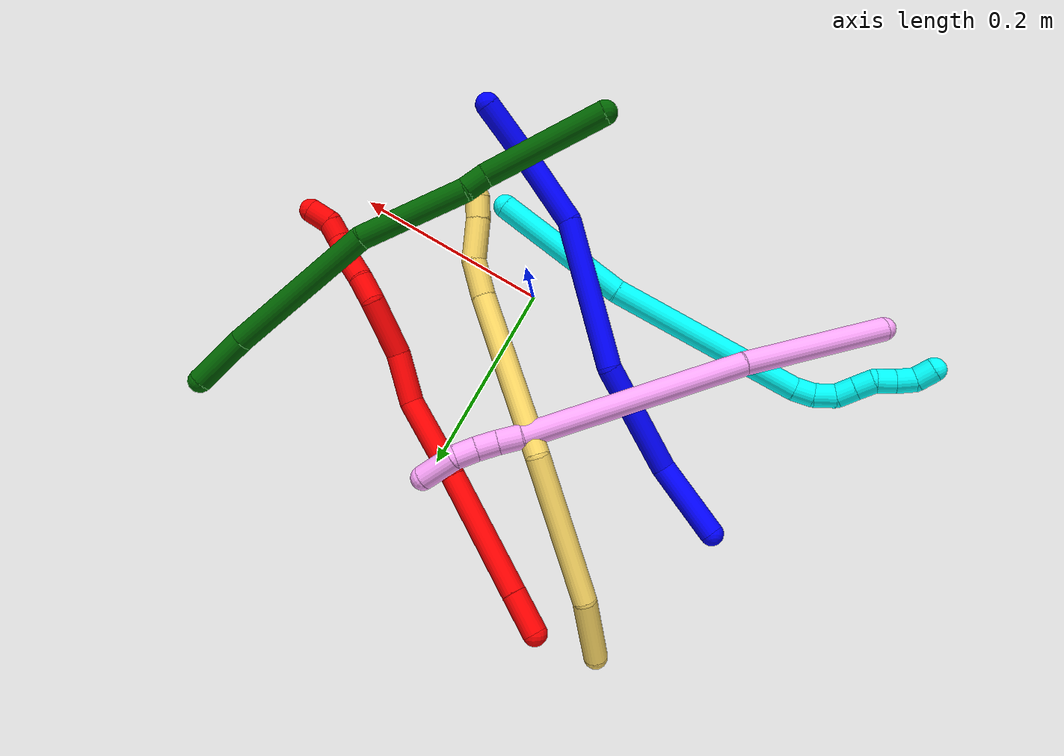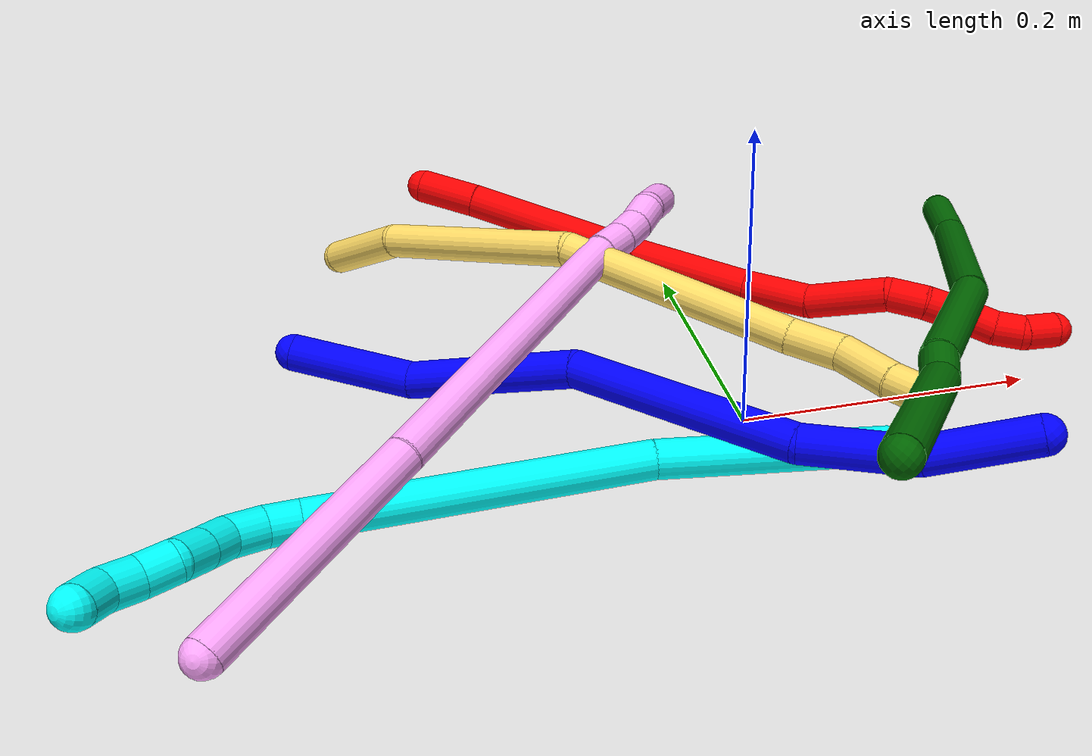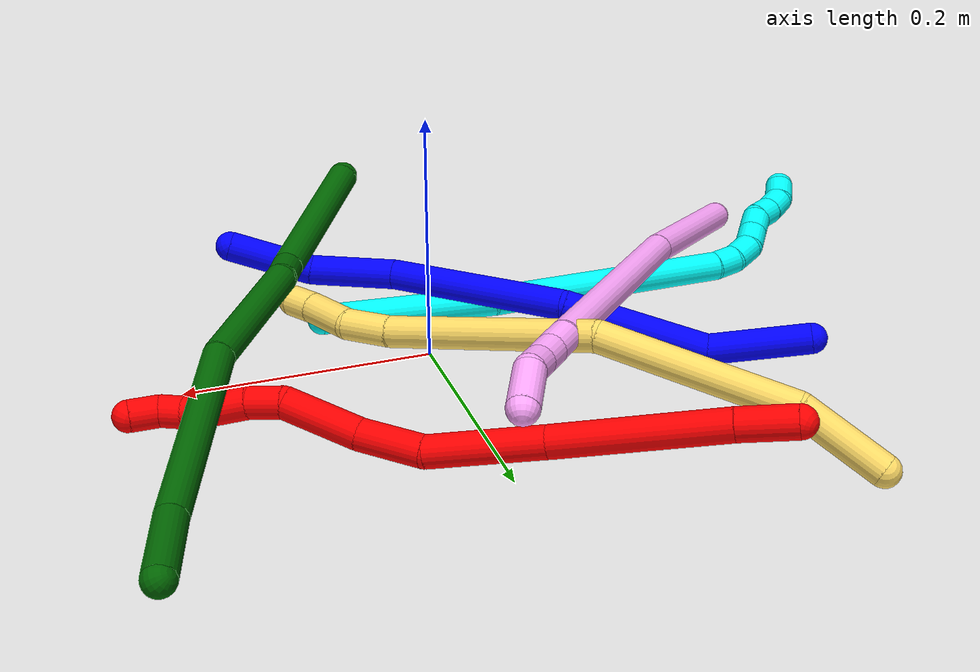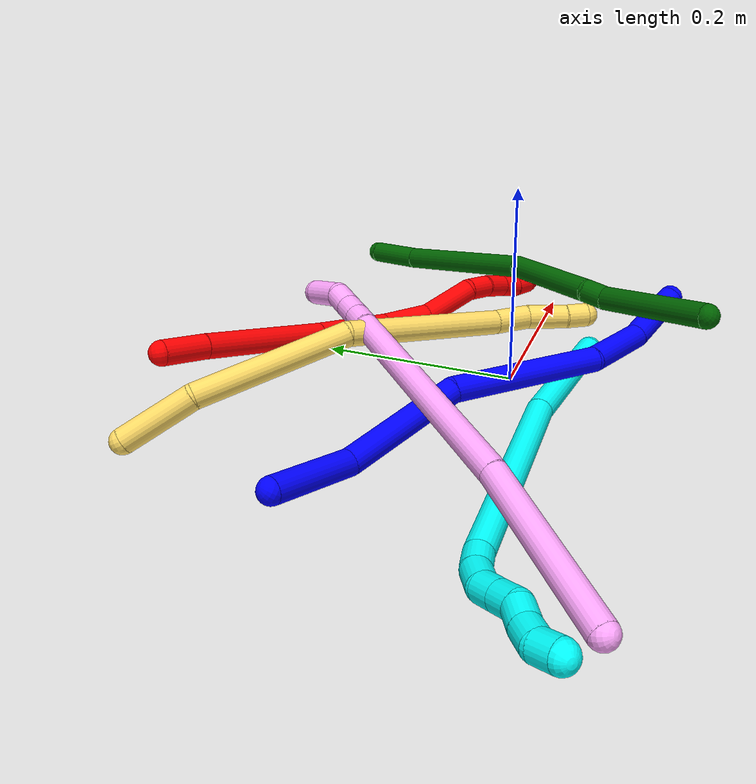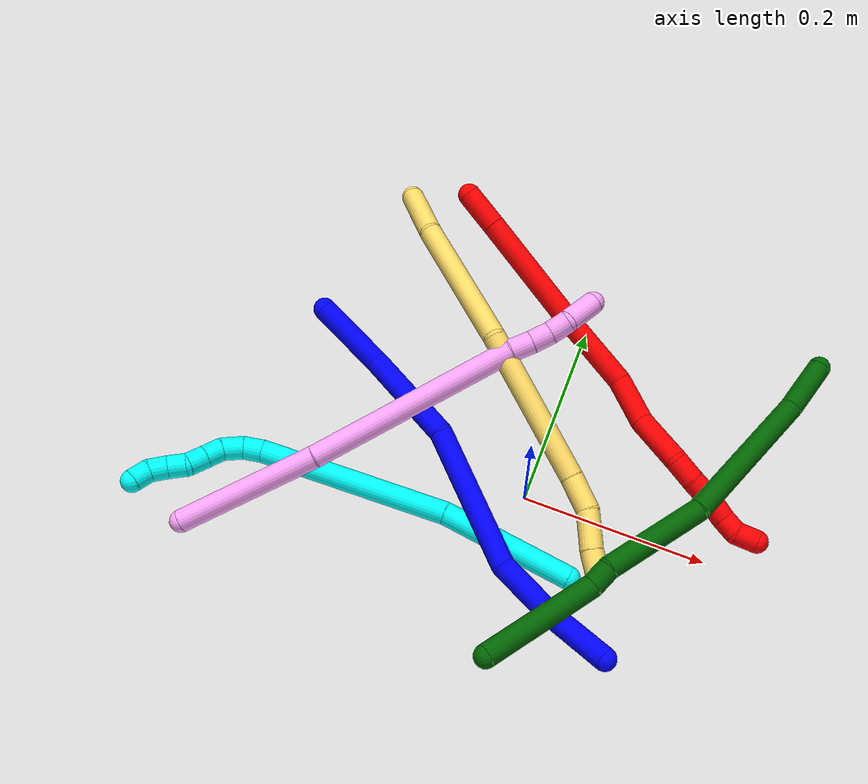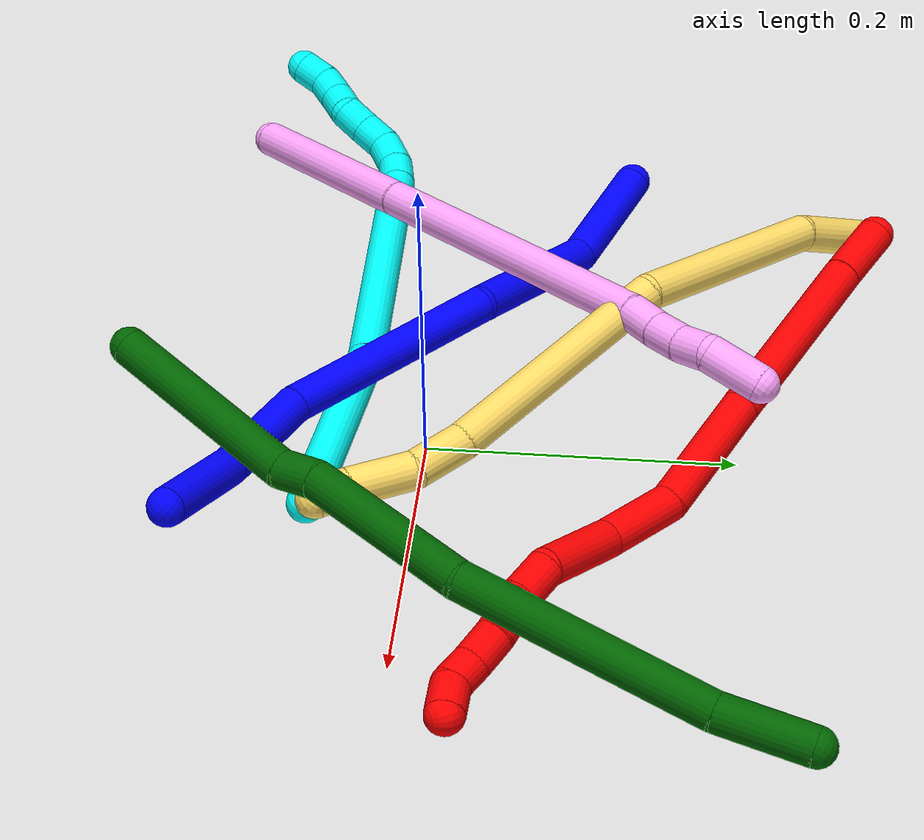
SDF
<sdf version="1.7">
 <world name="default">
  <plugin name="TubeGeneratorPlugin" filename="libtube_generator_plugin.so"/>
  <model name="photoneo_s_sensor">
   <static>1</static>
   <pose>0 0 2 1.57079 1.57079 3.14159</pose>
   <link name="link">
    <inertial><mass>0.1</mass></inertial>
    <sensor name="sensor" type="depth">
     <update_rate>30</update_rate>
     <camera>
      <horizontal_fov>1.22</horizontal_fov>
      <image><width>1920</width><height>1200</height><format>B8G8R8</format></image>
      <clip><near>0.1</near><far>4</far></clip>
      <depth_camera><output>points</output></depth_camera>
     </camera>
     <plugin name="camera_plugin" filename="libgazebo_ros_depth_camera.so">
      <baseline>0.2</baseline>
      <alwaysOn>1</alwaysOn>
      <updateRate>0.0</updateRate>
      <cameraName>camera_ir</cameraName>
      <imageTopicName>/camera/color/image_raw</imageTopicName>
      <cameraInfoTopicName>/camera/color/camera_info</cameraInfoTopicName>
      <depthImageTopicName>/camera/depth/image_raw</depthImageTopicName>
      <depthImageCameraInfoTopicName>/camera/depth/camera_info</depthImageCameraInfoTopicName>
      <pointCloudTopicName>/camera/depth/points</pointCloudTopicName>
      <frameName>fr_optical</frameName>
      <pointCloudCutoff>0.1</pointCloudCutoff>
      <pointCloudCutoffMax>2.0</pointCloudCutoffMax>
      <distortionK1>0</distortionK1>
      <distortionK2>0</distortionK2>
      <distortionK3>0</distortionK3>
      <distortionT1>0</distortionT1>
      <distortionT2>0</distortionT2>
      <CxPrime>0</CxPrime>
      <Cx>0</Cx>
      <Cy>0</Cy>
      <focalLength>0</focalLength>
      <hackBaseline>0</hackBaseline>
     </plugin>
    </sensor>
   </link>
  </model>
  <gravity>0 0 -9.8</gravity>
  <magnetic_field>6e-06 2.3e-05 -4.2e-05</magnetic_field>
  <atmosphere type="adiabatic"/>
  <physics name="default_physics" default="0" type="ode">
   <max_step_size>0.003</max_step_size>
   <real_time_factor>1</real_time_factor>
   <real_time_update_rate>1000</real_time_update_rate>
   <max_contacts>10000</max_contacts>
   <ode>
    <solver>
     <type>quick</type>
     <iters>100</iters>
     <sor>1.3</sor>
     <use_dynamic_moi_rescaling>0</use_dynamic_moi_rescaling>
    </solver>
    <constraints>
     <contact_max_correcting_vel>0</contact_max_correcting_vel>
     <contact_surface_layer>0.001</contact_surface_layer>
     <cfm>0</cfm>
     <erp>0.2</erp>
    </constraints>
   </ode>
  </physics>
  <scene><ambient>0.4 0.4 0.4 1</ambient><background>0.7 0.7 0.7 1</background><shadows>0</shadows></scene>
  <audio><device>default</device></audio>
  <spherical_coordinates>
   <surface_model>EARTH_WGS84</surface_model>
   <latitude_deg>0</latitude_deg>
   <longitude_deg>0</longitude_deg>
   <elevation>0</elevation>
   <heading_deg>0</heading_deg>
  </spherical_coordinates>
  <model name="bin">
   <static>1</static>
   <link name="bottom">
    <collision name="collision-bottom">
     <pose>0 0 -0.01 0 -0 0</pose>
     <geometry><box><size>0.8 0.6 0.02</size></box></geometry>
     <surface>
      <friction><ode><mu>100</mu><mu2>100</mu2></ode></friction>
      <contact><collide_bitmask>65535</collide_bitmask></contact>
     </surface>
    </collision>
   </link>
   <link name="west_wall">
    <collision name="collision-west_wall">
     <pose>-0.41 0 0.1 0 -0 0</pose>
     <geometry><box><size>0.02 0.6 0.2</size></box></geometry>
     <surface>
      <friction><ode><mu>100</mu><mu2>100</mu2></ode></friction>
      <contact><collide_bitmask>65535</collide_bitmask></contact>
     </surface>
    </collision>
   </link>
   <link name="east_wall">
    <collision name="collision-east_wall">
     <pose>0.41 0 0.1 0 -0 0</pose>
     <geometry><box><size>0.02 0.6 0.2</size></box></geometry>
     <surface>
      <friction><ode><mu>100</mu><mu2>100</mu2></ode></friction>
      <contact><collide_bitmask>65535</collide_bitmask></contact>
     </surface>
    </collision>
   </link>
   <link name="south_wall">
    <collision name="collision-south_wall">
     <pose>0 -0.31 0.1 0 -0 0</pose>
     <geometry><box><size>0.8 0.02 0.2</size></box></geometry>
     <surface>
      <friction><ode><mu>100</mu><mu2>100</mu2></ode></friction>
      <contact><collide_bitmask>65535</collide_bitmask></contact>
     </surface>
    </collision>
   </link>
   <link name="north_wall">
    <collision name="collision-north_wall">
     <pose>0 0.31 0.1 0 -0 0</pose>
     <geometry><box><size>0.8 0.02 0.2</size></box></geometry>
     <surface>
      <friction><ode><mu>100</mu><mu2>100</mu2></ode></friction>
      <contact><collide_bitmask>65535</collide_bitmask></contact>
     </surface>
    </collision>
   </link>
  </model>
  <model name="1">
   <static>0</static>
   <link name="1">
    <collision name="collision-cylinder-e_1_1_4">
     <pose>-0.026079 0.016703 -0.017185 -2.37041 -0.827614 1.64946</pose>
     <geometry><cylinder><radius>0.0125</radius><length>0.070837</length></cylinder></geometry>
     <surface>
      <friction><ode><mu>1.16</mu><mu2>1.16</mu2><slip1>0</slip1><slip2>0</slip2></ode></friction>
      <contact><ode><kp>1e+06</kp><kd>1</kd><max_vel>0</max_vel><min_depth>0.001</min_depth></ode></contact>
     </surface>
    </collision>
    <visual name="visual-cylinder-e_1_1_4">
     <pose>-0.026079 0.016703 -0.017185 -2.37041 -0.827614 1.64946</pose>
     <geometry><cylinder><radius>0.0125</radius><length>0.070837</length></cylinder></geometry>
     <material><ambient>0 0 1 1</ambient></material>
    </visual>
    <collision name="collision-cylinder-e_2_4_5">
     <pose>-0.071968 0.048904 -0.059811 -2.59446 -0.586838 1.64469</pose>
     <geometry><cylinder><radius>0.0125</radius><length>0.071549</length></cylinder></geometry>
     <surface>
      <friction><ode><mu>1.16</mu><mu2>1.16</mu2><slip1>0</slip1><slip2>0</slip2></ode></friction>
      <contact><ode><kp>1e+06</kp><kd>1</kd><max_vel>0</max_vel><min_depth>0.001</min_depth></ode></contact>
     </surface>
    </collision>
    <visual name="visual-cylinder-e_2_4_5">
     <pose>-0.071968 0.048904 -0.059811 -2.59446 -0.586838 1.64469</pose>
     <geometry><cylinder><radius>0.0125</radius><length>0.071549</length></cylinder></geometry>
     <material><ambient>0 0 1 1</ambient></material>
    </visual>
    <collision name="collision-cylinder-e_3_5_6">
     <pose>-0.136612 0.07338 -0.14793 -2.99932 -0.616133 2.70098</pose>
     <geometry><cylinder><radius>0.0125</radius><length>0.155167</length></cylinder></geometry>
     <surface>
      <friction><ode><mu>1.16</mu><mu2>1.16</mu2><slip1>0</slip1><slip2>0</slip2></ode></friction>
      <contact><ode><kp>1e+06</kp><kd>1</kd><max_vel>0</max_vel><min_depth>0.001</min_depth></ode></contact>
     </surface>
    </collision>
    <visual name="visual-cylinder-e_3_5_6">
     <pose>-0.136612 0.07338 -0.14793 -2.99932 -0.616133 2.70098</pose>
     <geometry><cylinder><radius>0.0125</radius><length>0.155167</length></cylinder></geometry>
     <material><ambient>0 0 1 1</ambient></material>
    </visual>
    <collision name="collision-cylinder-e_4_6_7">
     <pose>-0.225685 0.10287 -0.245341 -2.60815 -0.83149 2.03319</pose>
     <geometry><cylinder><radius>0.0125</radius><length>0.119737</length></cylinder></geometry>
     <surface>
      <friction><ode><mu>1.16</mu><mu2>1.16</mu2><slip1>0</slip1><slip2>0</slip2></ode></friction>
      <contact><ode><kp>1e+06</kp><kd>1</kd><max_vel>0</max_vel><min_depth>0.001</min_depth></ode></contact>
     </surface>
    </collision>
    <visual name="visual-cylinder-e_4_6_7">
     <pose>-0.225685 0.10287 -0.245341 -2.60815 -0.83149 2.03319</pose>
     <geometry><cylinder><radius>0.0125</radius><length>0.119737</length></cylinder></geometry>
     <material><ambient>0 0 1 1</ambient></material>
    </visual>
    <collision name="collision-cylinder-e_5_7_2">
     <pose>-0.286544 0.142146 -0.312967 -2.62319 -0.413563 1.33862</pose>
     <geometry><cylinder><radius>0.0125</radius><length>0.082709</length></cylinder></geometry>
     <surface>
      <friction><ode><mu>1.16</mu><mu2>1.16</mu2><slip1>0</slip1><slip2>0</slip2></ode></friction>
      <contact><ode><kp>1e+06</kp><kd>1</kd><max_vel>0</max_vel><min_depth>0.001</min_depth></ode></contact>
     </surface>
    </collision>
    <visual name="visual-cylinder-e_5_7_2">
     <pose>-0.286544 0.142146 -0.312967 -2.62319 -0.413563 1.33862</pose>
     <geometry><cylinder><radius>0.0125</radius><length>0.082709</length></cylinder></geometry>
     <material><ambient>0 0 1 1</ambient></material>
    </visual>
    <collision name="collision-sphere-2">
     <pose>-0.303163 0.160909 -0.34586 0 -0 0</pose>
     <geometry><sphere><radius>0.0125</radius></sphere></geometry>
     <surface>
      <friction><ode><mu>1.16</mu><mu2>1.16</mu2><slip1>0</slip1><slip2>0</slip2></ode></friction>
      <contact><ode><kp>1e+06</kp><kd>1</kd><max_vel>0</max_vel><min_depth>0.001</min_depth></ode></contact>
     </surface>
    </collision>
    <visual name="visual-sphere-2">
     <pose>-0.303163 0.160909 -0.34586 0 -0 0</pose>
     <geometry><sphere><radius>0.0125</radius></sphere></geometry>
     <material><ambient>0 0 1 1</ambient></material>
    </visual>
    <collision name="collision-sphere-7">
     <pose>-0.269924 0.123382 -0.280074 0 -0 0</pose>
     <geometry><sphere><radius>0.0125</radius></sphere></geometry>
     <surface>
      <friction><ode><mu>1.16</mu><mu2>1.16</mu2><slip1>0</slip1><slip2>0</slip2></ode></friction>
      <contact><ode><kp>1e+06</kp><kd>1</kd><max_vel>0</max_vel><min_depth>0.001</min_depth></ode></contact>
     </surface>
    </collision>
    <visual name="visual-sphere-7">
     <pose>-0.269924 0.123382 -0.280074 0 -0 0</pose>
     <geometry><sphere><radius>0.0125</radius></sphere></geometry>
     <material><ambient>0 0 1 1</ambient></material>
    </visual>
    <collision name="collision-sphere-6">
     <pose>-0.181446 0.082358 -0.210607 0 -0 0</pose>
     <geometry><sphere><radius>0.0125</radius></sphere></geometry>
     <surface>
      <friction><ode><mu>1.16</mu><mu2>1.16</mu2><slip1>0</slip1><slip2>0</slip2></ode></friction>
      <contact><ode><kp>1e+06</kp><kd>1</kd><max_vel>0</max_vel><min_depth>0.001</min_depth></ode></contact>
     </surface>
    </collision>
    <visual name="visual-sphere-6">
     <pose>-0.181446 0.082358 -0.210607 0 -0 0</pose>
     <geometry><sphere><radius>0.0125</radius></sphere></geometry>
     <material><ambient>0 0 1 1</ambient></material>
    </visual>
    <collision name="collision-sphere-5">
     <pose>-0.091778 0.064402 -0.085252 0 -0 0</pose>
     <geometry><sphere><radius>0.0125</radius></sphere></geometry>
     <surface>
      <friction><ode><mu>1.16</mu><mu2>1.16</mu2><slip1>0</slip1><slip2>0</slip2></ode></friction>
      <contact><ode><kp>1e+06</kp><kd>1</kd><max_vel>0</max_vel><min_depth>0.001</min_depth></ode></contact>
     </surface>
    </collision>
    <visual name="visual-sphere-5">
     <pose>-0.091778 0.064402 -0.085252 0 -0 0</pose>
     <geometry><sphere><radius>0.0125</radius></sphere></geometry>
     <material><ambient>0 0 1 1</ambient></material>
    </visual>
    <collision name="collision-sphere-1">
     <geometry><sphere><radius>0.0125</radius></sphere></geometry>
     <surface>
      <friction><ode><mu>1.16</mu><mu2>1.16</mu2><slip1>0</slip1><slip2>0</slip2></ode></friction>
      <contact><ode><kp>1e+06</kp><kd>1</kd><max_vel>0</max_vel><min_depth>0.001</min_depth></ode></contact>
     </surface>
    </collision>
    <visual name="visual-sphere-1">
     <geometry><sphere><radius>0.0125</radius></sphere></geometry>
     <material><ambient>0 0 1 1</ambient></material>
    </visual>
    <collision name="collision-sphere-4">
     <pose>-0.052158 0.033407 -0.03437 0 -0 0</pose>
     <geometry><sphere><radius>0.0125</radius></sphere></geometry>
     <surface>
      <friction><ode><mu>1.16</mu><mu2>1.16</mu2><slip1>0</slip1><slip2>0</slip2></ode></friction>
      <contact><ode><kp>1e+06</kp><kd>1</kd><max_vel>0</max_vel><min_depth>0.001</min_depth></ode></contact>
     </surface>
    </collision>
    <visual name="visual-sphere-4">
     <pose>-0.052158 0.033407 -0.03437 0 -0 0</pose>
     <geometry><sphere><radius>0.0125</radius></sphere></geometry>
     <material><ambient>0 0 1 1</ambient></material>
    </visual>
    <inertial>
     <pose>-0.157834 0.080285 -0.167425 0 -0 0</pose>
     <mass>0.5</mass>
     <inertia><ixx>-2e-06</ixx><ixy>0</ixy><ixz>0</ixz><iyy>0.000738</iyy><iyz>0</iyz><izz>0.000188</izz></inertia>
    </inertial>
   </link>
   <pose>0.132368 -0.138802 0.056221 3.12278 -0.922773 -0.882583</pose>
  </model>
  <model name="2">
   <static>0</static>
   <link name="2">
    <collision name="collision-cylinder-e_1_1_4">
     <pose>0.0088 -0.0065 -0.018829 2.8092 0.416017 1.79851</pose>
     <geometry><cylinder><radius>0.0125</radius><length>0.043554</length></cylinder></geometry>
     <surface>
      <friction><ode><mu>1.16</mu><mu2>1.16</mu2><slip1>0</slip1><slip2>0</slip2></ode></friction>
      <contact><ode><kp>1e+06</kp><kd>1</kd><max_vel>0</max_vel><min_depth>0.001</min_depth></ode></contact>
     </surface>
    </collision>
    <visual name="visual-cylinder-e_1_1_4">
     <pose>0.0088 -0.0065 -0.018829 2.8092 0.416017 1.79851</pose>
     <geometry><cylinder><radius>0.0125</radius><length>0.043554</length></cylinder></geometry>
     <material><ambient>1 0 0 1</ambient></material>
    </visual>
    <collision name="collision-cylinder-e_2_4_5">
     <pose>0.046963 -0.031089 -0.093341 2.82748 0.46485 1.96234</pose>
     <geometry><cylinder><radius>0.0125</radius><length>0.130996</length></cylinder></geometry>
     <surface>
      <friction><ode><mu>1.16</mu><mu2>1.16</mu2><slip1>0</slip1><slip2>0</slip2></ode></friction>
      <contact><ode><kp>1e+06</kp><kd>1</kd><max_vel>0</max_vel><min_depth>0.001</min_depth></ode></contact>
     </surface>
    </collision>
    <visual name="visual-cylinder-e_2_4_5">
     <pose>0.046963 -0.031089 -0.093341 2.82748 0.46485 1.96234</pose>
     <geometry><cylinder><radius>0.0125</radius><length>0.130996</length></cylinder></geometry>
     <material><ambient>1 0 0 1</ambient></material>
    </visual>
    <collision name="collision-cylinder-e_3_5_6">
     <pose>0.095811 -0.063214 -0.186856 2.78633 0.449891 1.81108</pose>
     <geometry><cylinder><radius>0.0125</radius><length>0.089619</length></cylinder></geometry>
     <surface>
      <friction><ode><mu>1.16</mu><mu2>1.16</mu2><slip1>0</slip1><slip2>0</slip2></ode></friction>
      <contact><ode><kp>1e+06</kp><kd>1</kd><max_vel>0</max_vel><min_depth>0.001</min_depth></ode></contact>
     </surface>
    </collision>
    <visual name="visual-cylinder-e_3_5_6">
     <pose>0.095811 -0.063214 -0.186856 2.78633 0.449891 1.81108</pose>
     <geometry><cylinder><radius>0.0125</radius><length>0.089619</length></cylinder></geometry>
     <material><ambient>1 0 0 1</ambient></material>
    </visual>
    <collision name="collision-cylinder-e_4_6_7">
     <pose>0.119128 -0.082254 -0.250364 2.94909 0.145408 1.29258</pose>
     <geometry><cylinder><radius>0.0125</radius><length>0.052879</length></cylinder></geometry>
     <surface>
      <friction><ode><mu>1.16</mu><mu2>1.16</mu2><slip1>0</slip1><slip2>0</slip2></ode></friction>
      <contact><ode><kp>1e+06</kp><kd>1</kd><max_vel>0</max_vel><min_depth>0.001</min_depth></ode></contact>
     </surface>
    </collision>
    <visual name="visual-cylinder-e_4_6_7">
     <pose>0.119128 -0.082254 -0.250364 2.94909 0.145408 1.29258</pose>
     <geometry><cylinder><radius>0.0125</radius><length>0.052879</length></cylinder></geometry>
     <material><ambient>1 0 0 1</ambient></material>
    </visual>
    <collision name="collision-cylinder-e_5_7_8">
     <pose>0.121841 -0.099973 -0.303377 2.70623 -0.037069 -0.167223</pose>
     <geometry><cylinder><radius>0.0125</radius><length>0.060337</length></cylinder></geometry>
     <surface>
      <friction><ode><mu>1.16</mu><mu2>1.16</mu2><slip1>0</slip1><slip2>0</slip2></ode></friction>
      <contact><ode><kp>1e+06</kp><kd>1</kd><max_vel>0</max_vel><min_depth>0.001</min_depth></ode></contact>
     </surface>
    </collision>
    <visual name="visual-cylinder-e_5_7_8">
     <pose>0.121841 -0.099973 -0.303377 2.70623 -0.037069 -0.167223</pose>
     <geometry><cylinder><radius>0.0125</radius><length>0.060337</length></cylinder></geometry>
     <material><ambient>1 0 0 1</ambient></material>
    </visual>
    <collision name="collision-cylinder-e_6_8_9">
     <pose>0.125536 -0.117122 -0.342567 2.78365 0.363392 1.58625</pose>
     <geometry><cylinder><radius>0.0125</radius><length>0.027083</length></cylinder></geometry>
     <surface>
      <friction><ode><mu>1.16</mu><mu2>1.16</mu2><slip1>0</slip1><slip2>0</slip2></ode></friction>
      <contact><ode><kp>1e+06</kp><kd>1</kd><max_vel>0</max_vel><min_depth>0.001</min_depth></ode></contact>
     </surface>
    </collision>
    <visual name="visual-cylinder-e_6_8_9">
     <pose>0.125536 -0.117122 -0.342567 2.78365 0.363392 1.58625</pose>
     <geometry><cylinder><radius>0.0125</radius><length>0.027083</length></cylinder></geometry>
     <material><ambient>1 0 0 1</ambient></material>
    </visual>
    <collision name="collision-cylinder-e_7_9_10">
     <pose>0.137756 -0.126004 -0.365875 2.77117 0.542514 1.95592</pose>
     <geometry><cylinder><radius>0.0125</radius><length>0.028692</length></cylinder></geometry>
     <surface>
      <friction><ode><mu>1.16</mu><mu2>1.16</mu2><slip1>0</slip1><slip2>0</slip2></ode></friction>
      <contact><ode><kp>1e+06</kp><kd>1</kd><max_vel>0</max_vel><min_depth>0.001</min_depth></ode></contact>
     </surface>
    </collision>
    <visual name="visual-cylinder-e_7_9_10">
     <pose>0.137756 -0.126004 -0.365875 2.77117 0.542514 1.95592</pose>
     <geometry><cylinder><radius>0.0125</radius><length>0.028692</length></cylinder></geometry>
     <material><ambient>1 0 0 1</ambient></material>
    </visual>
    <collision name="collision-cylinder-e_8_10_11">
     <pose>0.15047 -0.132827 -0.387267 2.90696 0.478967 2.24218</pose>
     <geometry><cylinder><radius>0.0125</radius><length>0.023032</length></cylinder></geometry>
     <surface>
      <friction><ode><mu>1.16</mu><mu2>1.16</mu2><slip1>0</slip1><slip2>0</slip2></ode></friction>
      <contact><ode><kp>1e+06</kp><kd>1</kd><max_vel>0</max_vel><min_depth>0.001</min_depth></ode></contact>
     </surface>
    </collision>
    <visual name="visual-cylinder-e_8_10_11">
     <pose>0.15047 -0.132827 -0.387267 2.90696 0.478967 2.24218</pose>
     <geometry><cylinder><radius>0.0125</radius><length>0.023032</length></cylinder></geometry>
     <material><ambient>1 0 0 1</ambient></material>
    </visual>
    <collision name="collision-cylinder-e_9_11_12">
     <pose>0.158776 -0.138931 -0.406164 2.7472 0.299793 1.29458</pose>
     <geometry><cylinder><radius>0.0125</radius><length>0.020309</length></cylinder></geometry>
     <surface>
      <friction><ode><mu>1.16</mu><mu2>1.16</mu2><slip1>0</slip1><slip2>0</slip2></ode></friction>
      <contact><ode><kp>1e+06</kp><kd>1</kd><max_vel>0</max_vel><min_depth>0.001</min_depth></ode></contact>
     </surface>
    </collision>
    <visual name="visual-cylinder-e_9_11_12">
     <pose>0.158776 -0.138931 -0.406164 2.7472 0.299793 1.29458</pose>
     <geometry><cylinder><radius>0.0125</radius><length>0.020309</length></cylinder></geometry>
     <material><ambient>1 0 0 1</ambient></material>
    </visual>
    <collision name="collision-cylinder-e_10_12_2">
     <pose>0.16675 -0.150969 -0.421774 2.24596 0.437152 0.866254</pose>
     <geometry><cylinder><radius>0.0125</radius><length>0.023501</length></cylinder></geometry>
     <surface>
      <friction><ode><mu>1.16</mu><mu2>1.16</mu2><slip1>0</slip1><slip2>0</slip2></ode></friction>
      <contact><ode><kp>1e+06</kp><kd>1</kd><max_vel>0</max_vel><min_depth>0.001</min_depth></ode></contact>
     </surface>
    </collision>
    <visual name="visual-cylinder-e_10_12_2">
     <pose>0.16675 -0.150969 -0.421774 2.24596 0.437152 0.866254</pose>
     <geometry><cylinder><radius>0.0125</radius><length>0.023501</length></cylinder></geometry>
     <material><ambient>1 0 0 1</ambient></material>
    </visual>
    <collision name="collision-sphere-2">
     <pose>0.171724 -0.159278 -0.428428 0 -0 0</pose>
     <geometry><sphere><radius>0.0125</radius></sphere></geometry>
     <surface>
      <friction><ode><mu>1.16</mu><mu2>1.16</mu2><slip1>0</slip1><slip2>0</slip2></ode></friction>
      <contact><ode><kp>1e+06</kp><kd>1</kd><max_vel>0</max_vel><min_depth>0.001</min_depth></ode></contact>
     </surface>
    </collision>
    <visual name="visual-sphere-2">
     <pose>0.171724 -0.159278 -0.428428 0 -0 0</pose>
     <geometry><sphere><radius>0.0125</radius></sphere></geometry>
     <material><ambient>1 0 0 1</ambient></material>
    </visual>
    <collision name="collision-sphere-12">
     <pose>0.161775 -0.142659 -0.415121 0 -0 0</pose>
     <geometry><sphere><radius>0.0125</radius></sphere></geometry>
     <surface>
      <friction><ode><mu>1.16</mu><mu2>1.16</mu2><slip1>0</slip1><slip2>0</slip2></ode></friction>
      <contact><ode><kp>1e+06</kp><kd>1</kd><max_vel>0</max_vel><min_depth>0.001</min_depth></ode></contact>
     </surface>
    </collision>
    <visual name="visual-sphere-12">
     <pose>0.161775 -0.142659 -0.415121 0 -0 0</pose>
     <geometry><sphere><radius>0.0125</radius></sphere></geometry>
     <material><ambient>1 0 0 1</ambient></material>
    </visual>
    <collision name="collision-sphere-11">
     <pose>0.155778 -0.135203 -0.397207 0 -0 0</pose>
     <geometry><sphere><radius>0.0125</radius></sphere></geometry>
     <surface>
      <friction><ode><mu>1.16</mu><mu2>1.16</mu2><slip1>0</slip1><slip2>0</slip2></ode></friction>
      <contact><ode><kp>1e+06</kp><kd>1</kd><max_vel>0</max_vel><min_depth>0.001</min_depth></ode></contact>
     </surface>
    </collision>
    <visual name="visual-sphere-11">
     <pose>0.155778 -0.135203 -0.397207 0 -0 0</pose>
     <geometry><sphere><radius>0.0125</radius></sphere></geometry>
     <material><ambient>1 0 0 1</ambient></material>
    </visual>
    <collision name="collision-sphere-10">
     <pose>0.145163 -0.130451 -0.377327 0 -0 0</pose>
     <geometry><sphere><radius>0.0125</radius></sphere></geometry>
     <surface>
      <friction><ode><mu>1.16</mu><mu2>1.16</mu2><slip1>0</slip1><slip2>0</slip2></ode></friction>
      <contact><ode><kp>1e+06</kp><kd>1</kd><max_vel>0</max_vel><min_depth>0.001</min_depth></ode></contact>
     </surface>
    </collision>
    <visual name="visual-sphere-10">
     <pose>0.145163 -0.130451 -0.377327 0 -0 0</pose>
     <geometry><sphere><radius>0.0125</radius></sphere></geometry>
     <material><ambient>1 0 0 1</ambient></material>
    </visual>
    <collision name="collision-sphere-9">
     <pose>0.13035 -0.121556 -0.354422 0 -0 0</pose>
     <geometry><sphere><radius>0.0125</radius></sphere></geometry>
     <surface>
      <friction><ode><mu>1.16</mu><mu2>1.16</mu2><slip1>0</slip1><slip2>0</slip2></ode></friction>
      <contact><ode><kp>1e+06</kp><kd>1</kd><max_vel>0</max_vel><min_depth>0.001</min_depth></ode></contact>
     </surface>
    </collision>
    <visual name="visual-sphere-9">
     <pose>0.13035 -0.121556 -0.354422 0 -0 0</pose>
     <geometry><sphere><radius>0.0125</radius></sphere></geometry>
     <material><ambient>1 0 0 1</ambient></material>
    </visual>
    <collision name="collision-sphere-4">
     <pose>0.017601 -0.013 -0.037658 0 -0 0</pose>
     <geometry><sphere><radius>0.0125</radius></sphere></geometry>
     <surface>
      <friction><ode><mu>1.16</mu><mu2>1.16</mu2><slip1>0</slip1><slip2>0</slip2></ode></friction>
      <contact><ode><kp>1e+06</kp><kd>1</kd><max_vel>0</max_vel><min_depth>0.001</min_depth></ode></contact>
     </surface>
    </collision>
    <visual name="visual-sphere-4">
     <pose>0.017601 -0.013 -0.037658 0 -0 0</pose>
     <geometry><sphere><radius>0.0125</radius></sphere></geometry>
     <material><ambient>1 0 0 1</ambient></material>
    </visual>
    <collision name="collision-sphere-1">
     <geometry><sphere><radius>0.0125</radius></sphere></geometry>
     <surface>
      <friction><ode><mu>1.16</mu><mu2>1.16</mu2><slip1>0</slip1><slip2>0</slip2></ode></friction>
      <contact><ode><kp>1e+06</kp><kd>1</kd><max_vel>0</max_vel><min_depth>0.001</min_depth></ode></contact>
     </surface>
    </collision>
    <visual name="visual-sphere-1">
     <geometry><sphere><radius>0.0125</radius></sphere></geometry>
     <material><ambient>1 0 0 1</ambient></material>
    </visual>
    <collision name="collision-sphere-8">
     <pose>0.120723 -0.112687 -0.330712 0 -0 0</pose>
     <geometry><sphere><radius>0.0125</radius></sphere></geometry>
     <surface>
      <friction><ode><mu>1.16</mu><mu2>1.16</mu2><slip1>0</slip1><slip2>0</slip2></ode></friction>
      <contact><ode><kp>1e+06</kp><kd>1</kd><max_vel>0</max_vel><min_depth>0.001</min_depth></ode></contact>
     </surface>
    </collision>
    <visual name="visual-sphere-8">
     <pose>0.120723 -0.112687 -0.330712 0 -0 0</pose>
     <geometry><sphere><radius>0.0125</radius></sphere></geometry>
     <material><ambient>1 0 0 1</ambient></material>
    </visual>
    <collision name="collision-sphere-5">
     <pose>0.076325 -0.049179 -0.149025 0 -0 0</pose>
     <geometry><sphere><radius>0.0125</radius></sphere></geometry>
     <surface>
      <friction><ode><mu>1.16</mu><mu2>1.16</mu2><slip1>0</slip1><slip2>0</slip2></ode></friction>
      <contact><ode><kp>1e+06</kp><kd>1</kd><max_vel>0</max_vel><min_depth>0.001</min_depth></ode></contact>
     </surface>
    </collision>
    <visual name="visual-sphere-5">
     <pose>0.076325 -0.049179 -0.149025 0 -0 0</pose>
     <geometry><sphere><radius>0.0125</radius></sphere></geometry>
     <material><ambient>1 0 0 1</ambient></material>
    </visual>
    <collision name="collision-sphere-6">
     <pose>0.115297 -0.077249 -0.224687 0 -0 0</pose>
     <geometry><sphere><radius>0.0125</radius></sphere></geometry>
     <surface>
      <friction><ode><mu>1.16</mu><mu2>1.16</mu2><slip1>0</slip1><slip2>0</slip2></ode></friction>
      <contact><ode><kp>1e+06</kp><kd>1</kd><max_vel>0</max_vel><min_depth>0.001</min_depth></ode></contact>
     </surface>
    </collision>
    <visual name="visual-sphere-6">
     <pose>0.115297 -0.077249 -0.224687 0 -0 0</pose>
     <geometry><sphere><radius>0.0125</radius></sphere></geometry>
     <material><ambient>1 0 0 1</ambient></material>
    </visual>
    <collision name="collision-sphere-7">
     <pose>0.122959 -0.087259 -0.276041 0 -0 0</pose>
     <geometry><sphere><radius>0.0125</radius></sphere></geometry>
     <surface>
      <friction><ode><mu>1.16</mu><mu2>1.16</mu2><slip1>0</slip1><slip2>0</slip2></ode></friction>
      <contact><ode><kp>1e+06</kp><kd>1</kd><max_vel>0</max_vel><min_depth>0.001</min_depth></ode></contact>
     </surface>
    </collision>
    <visual name="visual-sphere-7">
     <pose>0.122959 -0.087259 -0.276041 0 -0 0</pose>
     <geometry><sphere><radius>0.0125</radius></sphere></geometry>
     <material><ambient>1 0 0 1</ambient></material>
    </visual>
    <inertial>
     <pose>0.093468 -0.073236 -0.216385 0 -0 0</pose>
     <mass>0.5</mass>
     <inertia>
      <ixx>0.000198</ixx>
      <ixy>0</ixy>
      <ixz>0</ixz>
      <iyy>0.000331</iyy>
      <iyz>0</iyz>
      <izz>-6.6e-05</izz>
     </inertia>
    </inertial>
   </link>
   <pose>-0.171657 0.287689 0.064657 -1.71237 1.09656 0.43697</pose>
  </model>
  <model name="3">
   <static>0</static>
   <link name="3">
    <collision name="collision-cylinder-e_1_1_4">
     <pose>-0.057995 0.01391 0.042408 -0.31694 -0.914892 0.157017</pose>
     <geometry><cylinder><radius>0.0125</radius><length>0.14636</length></cylinder></geometry>
     <surface>
      <friction><ode><mu>1.16</mu><mu2>1.16</mu2><slip1>0</slip1><slip2>0</slip2></ode></friction>
      <contact><ode><kp>1e+06</kp><kd>1</kd><max_vel>0</max_vel><min_depth>0.001</min_depth></ode></contact>
     </surface>
    </collision>
    <visual name="visual-cylinder-e_1_1_4">
     <pose>-0.057995 0.01391 0.042408 -0.31694 -0.914892 0.157017</pose>
     <geometry><cylinder><radius>0.0125</radius><length>0.14636</length></cylinder></geometry>
     <material><ambient>0.003922 1 0.996078 1</ambient></material>
    </visual>
    <collision name="collision-cylinder-e_2_4_5">
     <pose>-0.192415 0.036933 0.155402 -0.12841 -0.820971 0.055947</pose>
     <geometry><cylinder><radius>0.0125</radius><length>0.208865</length></cylinder></geometry>
     <surface>
      <friction><ode><mu>1.16</mu><mu2>1.16</mu2><slip1>0</slip1><slip2>0</slip2></ode></friction>
      <contact><ode><kp>1e+06</kp><kd>1</kd><max_vel>0</max_vel><min_depth>0.001</min_depth></ode></contact>
     </surface>
    </collision>
    <visual name="visual-cylinder-e_2_4_5">
     <pose>-0.192415 0.036933 0.155402 -0.12841 -0.820971 0.055947</pose>
     <geometry><cylinder><radius>0.0125</radius><length>0.208865</length></cylinder></geometry>
     <material><ambient>0.003922 1 0.996078 1</ambient></material>
    </visual>
    <collision name="collision-cylinder-e_3_5_6">
     <pose>-0.274986 0.046883 0.234509 -0.09769 -0.622638 0.031457</pose>
     <geometry><cylinder><radius>0.0125</radius><length>0.02108</length></cylinder></geometry>
     <surface>
      <friction><ode><mu>1.16</mu><mu2>1.16</mu2><slip1>0</slip1><slip2>0</slip2></ode></friction>
      <contact><ode><kp>1e+06</kp><kd>1</kd><max_vel>0</max_vel><min_depth>0.001</min_depth></ode></contact>
     </surface>
    </collision>
    <visual name="visual-cylinder-e_3_5_6">
     <pose>-0.274986 0.046883 0.234509 -0.09769 -0.622638 0.031457</pose>
     <geometry><cylinder><radius>0.0125</radius><length>0.02108</length></cylinder></geometry>
     <material><ambient>0.003922 1 0.996078 1</ambient></material>
    </visual>
    <collision name="collision-cylinder-e_4_6_7">
     <pose>-0.284782 0.047731 0.253936 -0.001228 -0.32289 0.0002</pose>
     <geometry><cylinder><radius>0.0125</radius><length>0.023</length></cylinder></geometry>
     <surface>
      <friction><ode><mu>1.16</mu><mu2>1.16</mu2><slip1>0</slip1><slip2>0</slip2></ode></friction>
      <contact><ode><kp>1e+06</kp><kd>1</kd><max_vel>0</max_vel><min_depth>0.001</min_depth></ode></contact>
     </surface>
    </collision>
    <visual name="visual-cylinder-e_4_6_7">
     <pose>-0.284782 0.047731 0.253936 -0.001228 -0.32289 0.0002</pose>
     <geometry><cylinder><radius>0.0125</radius><length>0.023</length></cylinder></geometry>
     <material><ambient>0.003922 1 0.996078 1</ambient></material>
    </visual>
    <collision name="collision-cylinder-e_5_7_8">
     <pose>-0.287299 0.046688 0.274817 0.105571 0.112354 0.005942</pose>
     <geometry><cylinder><radius>0.0125</radius><length>0.020189</length></cylinder></geometry>
     <surface>
      <friction><ode><mu>1.16</mu><mu2>1.16</mu2><slip1>0</slip1><slip2>0</slip2></ode></friction>
      <contact><ode><kp>1e+06</kp><kd>1</kd><max_vel>0</max_vel><min_depth>0.001</min_depth></ode></contact>
     </surface>
    </collision>
    <visual name="visual-cylinder-e_5_7_8">
     <pose>-0.287299 0.046688 0.274817 0.105571 0.112354 0.005942</pose>
     <geometry><cylinder><radius>0.0125</radius><length>0.020189</length></cylinder></geometry>
     <material><ambient>0.003922 1 0.996078 1</ambient></material>
    </visual>
    <collision name="collision-cylinder-e_6_8_9">
     <pose>-0.285062 0.044846 0.294761 0.078519 0.110111 0.004329</pose>
     <geometry><cylinder><radius>0.0125</radius><length>0.02012</length></cylinder></geometry>
     <surface>
      <friction><ode><mu>1.16</mu><mu2>1.16</mu2><slip1>0</slip1><slip2>0</slip2></ode></friction>
      <contact><ode><kp>1e+06</kp><kd>1</kd><max_vel>0</max_vel><min_depth>0.001</min_depth></ode></contact>
     </surface>
    </collision>
    <visual name="visual-cylinder-e_6_8_9">
     <pose>-0.285062 0.044846 0.294761 0.078519 0.110111 0.004329</pose>
     <geometry><cylinder><radius>0.0125</radius><length>0.02012</length></cylinder></geometry>
     <material><ambient>0.003922 1 0.996078 1</ambient></material>
    </visual>
    <collision name="collision-cylinder-e_7_9_10">
     <pose>-0.287856 0.042668 0.313971 0.14974 -0.395236 -0.030036</pose>
     <geometry><cylinder><radius>0.0125</radius><length>0.020254</length></cylinder></geometry>
     <surface>
      <friction><ode><mu>1.16</mu><mu2>1.16</mu2><slip1>0</slip1><slip2>0</slip2></ode></friction>
      <contact><ode><kp>1e+06</kp><kd>1</kd><max_vel>0</max_vel><min_depth>0.001</min_depth></ode></contact>
     </surface>
    </collision>
    <visual name="visual-cylinder-e_7_9_10">
     <pose>-0.287856 0.042668 0.313971 0.14974 -0.395236 -0.030036</pose>
     <geometry><cylinder><radius>0.0125</radius><length>0.020254</length></cylinder></geometry>
     <material><ambient>0.003922 1 0.996078 1</ambient></material>
    </visual>
    <collision name="collision-cylinder-e_8_10_11">
     <pose>-0.29396 0.040699 0.332979 0.058711 -0.221693 -0.006537</pose>
     <geometry><cylinder><radius>0.0125</radius><length>0.020057</length></cylinder></geometry>
     <surface>
      <friction><ode><mu>1.16</mu><mu2>1.16</mu2><slip1>0</slip1><slip2>0</slip2></ode></friction>
      <contact><ode><kp>1e+06</kp><kd>1</kd><max_vel>0</max_vel><min_depth>0.001</min_depth></ode></contact>
     </surface>
    </collision>
    <visual name="visual-cylinder-e_8_10_11">
     <pose>-0.29396 0.040699 0.332979 0.058711 -0.221693 -0.006537</pose>
     <geometry><cylinder><radius>0.0125</radius><length>0.020057</length></cylinder></geometry>
     <material><ambient>0.003922 1 0.996078 1</ambient></material>
    </visual>
    <collision name="collision-cylinder-e_9_11_2">
     <pose>-0.293987 0.038487 0.352405 0.167991 0.21876 0.018492</pose>
     <geometry><cylinder><radius>0.0125</radius><length>0.020073</length></cylinder></geometry>
     <surface>
      <friction><ode><mu>1.16</mu><mu2>1.16</mu2><slip1>0</slip1><slip2>0</slip2></ode></friction>
      <contact><ode><kp>1e+06</kp><kd>1</kd><max_vel>0</max_vel><min_depth>0.001</min_depth></ode></contact>
     </surface>
    </collision>
    <visual name="visual-cylinder-e_9_11_2">
     <pose>-0.293987 0.038487 0.352405 0.167991 0.21876 0.018492</pose>
     <geometry><cylinder><radius>0.0125</radius><length>0.020073</length></cylinder></geometry>
     <material><ambient>0.003922 1 0.996078 1</ambient></material>
    </visual>
    <collision name="collision-sphere-2">
     <pose>-0.291809 0.036849 0.362064 0 -0 0</pose>
     <geometry><sphere><radius>0.0125</radius></sphere></geometry>
     <surface>
      <friction><ode><mu>1.16</mu><mu2>1.16</mu2><slip1>0</slip1><slip2>0</slip2></ode></friction>
      <contact><ode><kp>1e+06</kp><kd>1</kd><max_vel>0</max_vel><min_depth>0.001</min_depth></ode></contact>
     </surface>
    </collision>
    <visual name="visual-sphere-2">
     <pose>-0.291809 0.036849 0.362064 0 -0 0</pose>
     <geometry><sphere><radius>0.0125</radius></sphere></geometry>
     <material><ambient>0.003922 1 0.996078 1</ambient></material>
    </visual>
    <collision name="collision-sphere-11">
     <pose>-0.296165 0.040125 0.342745 0 -0 0</pose>
     <geometry><sphere><radius>0.0125</radius></sphere></geometry>
     <surface>
      <friction><ode><mu>1.16</mu><mu2>1.16</mu2><slip1>0</slip1><slip2>0</slip2></ode></friction>
      <contact><ode><kp>1e+06</kp><kd>1</kd><max_vel>0</max_vel><min_depth>0.001</min_depth></ode></contact>
     </surface>
    </collision>
    <visual name="visual-sphere-11">
     <pose>-0.296165 0.040125 0.342745 0 -0 0</pose>
     <geometry><sphere><radius>0.0125</radius></sphere></geometry>
     <material><ambient>0.003922 1 0.996078 1</ambient></material>
    </visual>
    <collision name="collision-sphere-10">
     <pose>-0.291755 0.041273 0.323212 0 -0 0</pose>
     <geometry><sphere><radius>0.0125</radius></sphere></geometry>
     <surface>
      <friction><ode><mu>1.16</mu><mu2>1.16</mu2><slip1>0</slip1><slip2>0</slip2></ode></friction>
      <contact><ode><kp>1e+06</kp><kd>1</kd><max_vel>0</max_vel><min_depth>0.001</min_depth></ode></contact>
     </surface>
    </collision>
    <visual name="visual-sphere-10">
     <pose>-0.291755 0.041273 0.323212 0 -0 0</pose>
     <geometry><sphere><radius>0.0125</radius></sphere></geometry>
     <material><ambient>0.003922 1 0.996078 1</ambient></material>
    </visual>
    <collision name="collision-sphere-9">
     <pose>-0.283957 0.044062 0.304729 0 -0 0</pose>
     <geometry><sphere><radius>0.0125</radius></sphere></geometry>
     <surface>
      <friction><ode><mu>1.16</mu><mu2>1.16</mu2><slip1>0</slip1><slip2>0</slip2></ode></friction>
      <contact><ode><kp>1e+06</kp><kd>1</kd><max_vel>0</max_vel><min_depth>0.001</min_depth></ode></contact>
     </surface>
    </collision>
    <visual name="visual-sphere-9">
     <pose>-0.283957 0.044062 0.304729 0 -0 0</pose>
     <geometry><sphere><radius>0.0125</radius></sphere></geometry>
     <material><ambient>0.003922 1 0.996078 1</ambient></material>
    </visual>
    <collision name="collision-sphere-4">
     <pose>-0.11599 0.027819 0.084816 0 -0 0</pose>
     <geometry><sphere><radius>0.0125</radius></sphere></geometry>
     <surface>
      <friction><ode><mu>1.16</mu><mu2>1.16</mu2><slip1>0</slip1><slip2>0</slip2></ode></friction>
      <contact><ode><kp>1e+06</kp><kd>1</kd><max_vel>0</max_vel><min_depth>0.001</min_depth></ode></contact>
     </surface>
    </collision>
    <visual name="visual-sphere-4">
     <pose>-0.11599 0.027819 0.084816 0 -0 0</pose>
     <geometry><sphere><radius>0.0125</radius></sphere></geometry>
     <material><ambient>0.003922 1 0.996078 1</ambient></material>
    </visual>
    <collision name="collision-sphere-1">
     <geometry><sphere><radius>0.0125</radius></sphere></geometry>
     <surface>
      <friction><ode><mu>1.16</mu><mu2>1.16</mu2><slip1>0</slip1><slip2>0</slip2></ode></friction>
      <contact><ode><kp>1e+06</kp><kd>1</kd><max_vel>0</max_vel><min_depth>0.001</min_depth></ode></contact>
     </surface>
    </collision>
    <visual name="visual-sphere-1">
     <geometry><sphere><radius>0.0125</radius></sphere></geometry>
     <material><ambient>0.003922 1 0.996078 1</ambient></material>
    </visual>
    <collision name="collision-sphere-8">
     <pose>-0.286167 0.04563 0.284792 0 -0 0</pose>
     <geometry><sphere><radius>0.0125</radius></sphere></geometry>
     <surface>
      <friction><ode><mu>1.16</mu><mu2>1.16</mu2><slip1>0</slip1><slip2>0</slip2></ode></friction>
      <contact><ode><kp>1e+06</kp><kd>1</kd><max_vel>0</max_vel><min_depth>0.001</min_depth></ode></contact>
     </surface>
    </collision>
    <visual name="visual-sphere-8">
     <pose>-0.286167 0.04563 0.284792 0 -0 0</pose>
     <geometry><sphere><radius>0.0125</radius></sphere></geometry>
     <material><ambient>0.003922 1 0.996078 1</ambient></material>
    </visual>
    <collision name="collision-sphere-5">
     <pose>-0.268839 0.046048 0.225988 0 -0 0</pose>
     <geometry><sphere><radius>0.0125</radius></sphere></geometry>
     <surface>
      <friction><ode><mu>1.16</mu><mu2>1.16</mu2><slip1>0</slip1><slip2>0</slip2></ode></friction>
      <contact><ode><kp>1e+06</kp><kd>1</kd><max_vel>0</max_vel><min_depth>0.001</min_depth></ode></contact>
     </surface>
    </collision>
    <visual name="visual-sphere-5">
     <pose>-0.268839 0.046048 0.225988 0 -0 0</pose>
     <geometry><sphere><radius>0.0125</radius></sphere></geometry>
     <material><ambient>0.003922 1 0.996078 1</ambient></material>
    </visual>
    <collision name="collision-sphere-6">
     <pose>-0.281133 0.047718 0.24303 0 -0 0</pose>
     <geometry><sphere><radius>0.0125</radius></sphere></geometry>
     <surface>
      <friction><ode><mu>1.16</mu><mu2>1.16</mu2><slip1>0</slip1><slip2>0</slip2></ode></friction>
      <contact><ode><kp>1e+06</kp><kd>1</kd><max_vel>0</max_vel><min_depth>0.001</min_depth></ode></contact>
     </surface>
    </collision>
    <visual name="visual-sphere-6">
     <pose>-0.281133 0.047718 0.24303 0 -0 0</pose>
     <geometry><sphere><radius>0.0125</radius></sphere></geometry>
     <material><ambient>0.003922 1 0.996078 1</ambient></material>
    </visual>
    <collision name="collision-sphere-7">
     <pose>-0.288431 0.047745 0.264842 0 -0 0</pose>
     <geometry><sphere><radius>0.0125</radius></sphere></geometry>
     <surface>
      <friction><ode><mu>1.16</mu><mu2>1.16</mu2><slip1>0</slip1><slip2>0</slip2></ode></friction>
      <contact><ode><kp>1e+06</kp><kd>1</kd><max_vel>0</max_vel><min_depth>0.001</min_depth></ode></contact>
     </surface>
    </collision>
    <visual name="visual-sphere-7">
     <pose>-0.288431 0.047745 0.264842 0 -0 0</pose>
     <geometry><sphere><radius>0.0125</radius></sphere></geometry>
     <material><ambient>0.003922 1 0.996078 1</ambient></material>
    </visual>
    <inertial>
     <pose>-0.180374 0.032268 0.162079 0 -0 0</pose>
     <mass>0.5</mass>
     <inertia>
      <ixx>0.000725</ixx>
      <ixy>0</ixy>
      <ixz>0</ixz>
      <iyy>0.001093</iyy>
      <iyz>0</iyz>
      <izz>0.000686</izz>
     </inertia>
    </inertial>
   </link>
   <pose>0.072518 -0.066677 0.011493 1.17518 -0.446797 -0.608859</pose>
  </model>
  <model name="4">
   <static>0</static>
   <link name="4">
    <collision name="collision-cylinder-e_1_1_4">
     <pose>0.024531 0.049879 0.056201 -0.725874 0.31555 -0.120691</pose>
     <geometry><cylinder><radius>0.0125</radius><length>0.158091</length></cylinder></geometry>
     <surface>
      <friction><ode><mu>1.16</mu><mu2>1.16</mu2><slip1>0</slip1><slip2>0</slip2></ode></friction>
      <contact><ode><kp>1e+06</kp><kd>1</kd><max_vel>0</max_vel><min_depth>0.001</min_depth></ode></contact>
     </surface>
    </collision>
    <visual name="visual-cylinder-e_1_1_4">
     <pose>0.024531 0.049879 0.056201 -0.725874 0.31555 -0.120691</pose>
     <geometry><cylinder><radius>0.0125</radius><length>0.158091</length></cylinder></geometry>
     <material><ambient>1 0.65098 0.996078 1</ambient></material>
    </visual>
    <collision name="collision-cylinder-e_2_4_5">
     <pose>0.085018 0.165141 0.202749 -0.626444 0.311882 -0.101752</pose>
     <geometry><cylinder><radius>0.0125</radius><length>0.234355</length></cylinder></geometry>
     <surface>
      <friction><ode><mu>1.16</mu><mu2>1.16</mu2><slip1>0</slip1><slip2>0</slip2></ode></friction>
      <contact><ode><kp>1e+06</kp><kd>1</kd><max_vel>0</max_vel><min_depth>0.001</min_depth></ode></contact>
     </surface>
    </collision>
    <visual name="visual-cylinder-e_2_4_5">
     <pose>0.085018 0.165141 0.202749 -0.626444 0.311882 -0.101752</pose>
     <geometry><cylinder><radius>0.0125</radius><length>0.234355</length></cylinder></geometry>
     <material><ambient>1 0.65098 0.996078 1</ambient></material>
    </visual>
    <collision name="collision-cylinder-e_3_5_6">
     <pose>0.123102 0.23736 0.302876 -0.610081 0.176548 -0.05572</pose>
     <geometry><cylinder><radius>0.0125</radius><length>0.024238</length></cylinder></geometry>
     <surface>
      <friction><ode><mu>1.16</mu><mu2>1.16</mu2><slip1>0</slip1><slip2>0</slip2></ode></friction>
      <contact><ode><kp>1e+06</kp><kd>1</kd><max_vel>0</max_vel><min_depth>0.001</min_depth></ode></contact>
     </surface>
    </collision>
    <visual name="visual-cylinder-e_3_5_6">
     <pose>0.123102 0.23736 0.302876 -0.610081 0.176548 -0.05572</pose>
     <geometry><cylinder><radius>0.0125</radius><length>0.024238</length></cylinder></geometry>
     <material><ambient>1 0.65098 0.996078 1</ambient></material>
    </visual>
    <collision name="collision-cylinder-e_4_6_7">
     <pose>0.128114 0.250416 0.321586 -0.608364 0.258964 -0.081707</pose>
     <geometry><cylinder><radius>0.0125</radius><length>0.02252</length></cylinder></geometry>
     <surface>
      <friction><ode><mu>1.16</mu><mu2>1.16</mu2><slip1>0</slip1><slip2>0</slip2></ode></friction>
      <contact><ode><kp>1e+06</kp><kd>1</kd><max_vel>0</max_vel><min_depth>0.001</min_depth></ode></contact>
     </surface>
    </collision>
    <visual name="visual-cylinder-e_4_6_7">
     <pose>0.128114 0.250416 0.321586 -0.608364 0.258964 -0.081707</pose>
     <geometry><cylinder><radius>0.0125</radius><length>0.02252</length></cylinder></geometry>
     <material><ambient>1 0.65098 0.996078 1</ambient></material>
    </visual>
    <collision name="collision-cylinder-e_5_7_8">
     <pose>0.135449 0.262661 0.338803 -0.628655 0.409888 -0.134949</pose>
     <geometry><cylinder><radius>0.0125</radius><length>0.022339</length></cylinder></geometry>
     <surface>
      <friction><ode><mu>1.16</mu><mu2>1.16</mu2><slip1>0</slip1><slip2>0</slip2></ode></friction>
      <contact><ode><kp>1e+06</kp><kd>1</kd><max_vel>0</max_vel><min_depth>0.001</min_depth></ode></contact>
     </surface>
    </collision>
    <visual name="visual-cylinder-e_5_7_8">
     <pose>0.135449 0.262661 0.338803 -0.628655 0.409888 -0.134949</pose>
     <geometry><cylinder><radius>0.0125</radius><length>0.022339</length></cylinder></geometry>
     <material><ambient>1 0.65098 0.996078 1</ambient></material>
    </visual>
    <collision name="collision-cylinder-e_6_8_2">
     <pose>0.143143 0.272419 0.365671 -0.198313 0.169476 -0.0169</pose>
     <geometry><cylinder><radius>0.0125</radius><length>0.038457</length></cylinder></geometry>
     <surface>
      <friction><ode><mu>1.16</mu><mu2>1.16</mu2><slip1>0</slip1><slip2>0</slip2></ode></friction>
      <contact><ode><kp>1e+06</kp><kd>1</kd><max_vel>0</max_vel><min_depth>0.001</min_depth></ode></contact>
     </surface>
    </collision>
    <visual name="visual-cylinder-e_6_8_2">
     <pose>0.143143 0.272419 0.365671 -0.198313 0.169476 -0.0169</pose>
     <geometry><cylinder><radius>0.0125</radius><length>0.038457</length></cylinder></geometry>
     <material><ambient>1 0.65098 0.996078 1</ambient></material>
    </visual>
    <collision name="collision-sphere-2">
     <pose>0.146386 0.276153 0.384252 0 -0 0</pose>
     <geometry><sphere><radius>0.0125</radius></sphere></geometry>
     <surface>
      <friction><ode><mu>1.16</mu><mu2>1.16</mu2><slip1>0</slip1><slip2>0</slip2></ode></friction>
      <contact><ode><kp>1e+06</kp><kd>1</kd><max_vel>0</max_vel><min_depth>0.001</min_depth></ode></contact>
     </surface>
    </collision>
    <visual name="visual-sphere-2">
     <pose>0.146386 0.276153 0.384252 0 -0 0</pose>
     <geometry><sphere><radius>0.0125</radius></sphere></geometry>
     <material><ambient>1 0.65098 0.996078 1</ambient></material>
    </visual>
    <collision name="collision-sphere-4">
     <pose>0.049062 0.099758 0.112401 0 -0 0</pose>
     <geometry><sphere><radius>0.0125</radius></sphere></geometry>
     <surface>
      <friction><ode><mu>1.16</mu><mu2>1.16</mu2><slip1>0</slip1><slip2>0</slip2></ode></friction>
      <contact><ode><kp>1e+06</kp><kd>1</kd><max_vel>0</max_vel><min_depth>0.001</min_depth></ode></contact>
     </surface>
    </collision>
    <visual name="visual-sphere-4">
     <pose>0.049062 0.099758 0.112401 0 -0 0</pose>
     <geometry><sphere><radius>0.0125</radius></sphere></geometry>
     <material><ambient>1 0.65098 0.996078 1</ambient></material>
    </visual>
    <collision name="collision-sphere-1">
     <geometry><sphere><radius>0.0125</radius></sphere></geometry>
     <surface>
      <friction><ode><mu>1.16</mu><mu2>1.16</mu2><slip1>0</slip1><slip2>0</slip2></ode></friction>
      <contact><ode><kp>1e+06</kp><kd>1</kd><max_vel>0</max_vel><min_depth>0.001</min_depth></ode></contact>
     </surface>
    </collision>
    <visual name="visual-sphere-1">
     <geometry><sphere><radius>0.0125</radius></sphere></geometry>
     <material><ambient>1 0.65098 0.996078 1</ambient></material>
    </visual>
    <collision name="collision-sphere-8">
     <pose>0.1399 0.268685 0.347089 0 -0 0</pose>
     <geometry><sphere><radius>0.0125</radius></sphere></geometry>
     <surface>
      <friction><ode><mu>1.16</mu><mu2>1.16</mu2><slip1>0</slip1><slip2>0</slip2></ode></friction>
      <contact><ode><kp>1e+06</kp><kd>1</kd><max_vel>0</max_vel><min_depth>0.001</min_depth></ode></contact>
     </surface>
    </collision>
    <visual name="visual-sphere-8">
     <pose>0.1399 0.268685 0.347089 0 -0 0</pose>
     <geometry><sphere><radius>0.0125</radius></sphere></geometry>
     <material><ambient>1 0.65098 0.996078 1</ambient></material>
    </visual>
    <collision name="collision-sphere-5">
     <pose>0.120974 0.230524 0.293098 0 -0 0</pose>
     <geometry><sphere><radius>0.0125</radius></sphere></geometry>
     <surface>
      <friction><ode><mu>1.16</mu><mu2>1.16</mu2><slip1>0</slip1><slip2>0</slip2></ode></friction>
      <contact><ode><kp>1e+06</kp><kd>1</kd><max_vel>0</max_vel><min_depth>0.001</min_depth></ode></contact>
     </surface>
    </collision>
    <visual name="visual-sphere-5">
     <pose>0.120974 0.230524 0.293098 0 -0 0</pose>
     <geometry><sphere><radius>0.0125</radius></sphere></geometry>
     <material><ambient>1 0.65098 0.996078 1</ambient></material>
    </visual>
    <collision name="collision-sphere-6">
     <pose>0.125231 0.244195 0.312654 0 -0 0</pose>
     <geometry><sphere><radius>0.0125</radius></sphere></geometry>
     <surface>
      <friction><ode><mu>1.16</mu><mu2>1.16</mu2><slip1>0</slip1><slip2>0</slip2></ode></friction>
      <contact><ode><kp>1e+06</kp><kd>1</kd><max_vel>0</max_vel><min_depth>0.001</min_depth></ode></contact>
     </surface>
    </collision>
    <visual name="visual-sphere-6">
     <pose>0.125231 0.244195 0.312654 0 -0 0</pose>
     <geometry><sphere><radius>0.0125</radius></sphere></geometry>
     <material><ambient>1 0.65098 0.996078 1</ambient></material>
    </visual>
    <collision name="collision-sphere-7">
     <pose>0.130998 0.256637 0.330517 0 -0 0</pose>
     <geometry><sphere><radius>0.0125</radius></sphere></geometry>
     <surface>
      <friction><ode><mu>1.16</mu><mu2>1.16</mu2><slip1>0</slip1><slip2>0</slip2></ode></friction>
      <contact><ode><kp>1e+06</kp><kd>1</kd><max_vel>0</max_vel><min_depth>0.001</min_depth></ode></contact>
     </surface>
    </collision>
    <visual name="visual-sphere-7">
     <pose>0.130998 0.256637 0.330517 0 -0 0</pose>
     <geometry><sphere><radius>0.0125</radius></sphere></geometry>
     <material><ambient>1 0.65098 0.996078 1</ambient></material>
    </visual>
    <inertial>
     <pose>0.076404 0.148647 0.185229 0 -0 0</pose>
     <mass>0.5</mass>
     <inertia>
      <ixx>0.00122</ixx>
      <ixy>0</ixy>
      <ixz>0</ixz>
      <iyy>0.001038</iyy>
      <iyz>0</iyz>
      <izz>-0.001228</izz>
     </inertia>
    </inertial>
   </link>
   <pose>-0.33153 -0.153171 0.012599 2.38536 -0.868447 2.06927</pose>
  </model>
  <model name="5">
   <static>0</static>
   <link name="5">
    <collision name="collision-cylinder-e_1_1_4">
     <pose>0.024107 -0.025748 0.007158 1.29963 0.733947 0.568386</pose>
     <geometry><cylinder><radius>0.0125</radius><length>0.071983</length></cylinder></geometry>
     <surface>
      <friction><ode><mu>1.16</mu><mu2>1.16</mu2><slip1>0</slip1><slip2>0</slip2></ode></friction>
      <contact><ode><kp>1e+06</kp><kd>1</kd><max_vel>0</max_vel><min_depth>0.001</min_depth></ode></contact>
     </surface>
    </collision>
    <visual name="visual-cylinder-e_1_1_4">
     <pose>0.024107 -0.025748 0.007158 1.29963 0.733947 0.568386</pose>
     <geometry><cylinder><radius>0.0125</radius><length>0.071983</length></cylinder></geometry>
     <material><ambient>1 0.858824 0.4 1</ambient></material>
    </visual>
    <collision name="collision-cylinder-e_2_4_5">
     <pose>0.113426 -0.092715 0.016612 1.51518 1.00643 0.960121</pose>
     <geometry><cylinder><radius>0.0125</radius><length>0.154359</length></cylinder></geometry>
     <surface>
      <friction><ode><mu>1.16</mu><mu2>1.16</mu2><slip1>0</slip1><slip2>0</slip2></ode></friction>
      <contact><ode><kp>1e+06</kp><kd>1</kd><max_vel>0</max_vel><min_depth>0.001</min_depth></ode></contact>
     </surface>
    </collision>
    <visual name="visual-cylinder-e_2_4_5">
     <pose>0.113426 -0.092715 0.016612 1.51518 1.00643 0.960121</pose>
     <geometry><cylinder><radius>0.0125</radius><length>0.154359</length></cylinder></geometry>
     <material><ambient>1 0.858824 0.4 1</ambient></material>
    </visual>
    <collision name="collision-cylinder-e_3_5_6">
     <pose>0.256273 -0.162281 -0.00097 2.1823 1.15133 1.79028</pose>
     <geometry><cylinder><radius>0.0125</radius><length>0.170012</length></cylinder></geometry>
     <surface>
      <friction><ode><mu>1.16</mu><mu2>1.16</mu2><slip1>0</slip1><slip2>0</slip2></ode></friction>
      <contact><ode><kp>1e+06</kp><kd>1</kd><max_vel>0</max_vel><min_depth>0.001</min_depth></ode></contact>
     </surface>
    </collision>
    <visual name="visual-cylinder-e_3_5_6">
     <pose>0.256273 -0.162281 -0.00097 2.1823 1.15133 1.79028</pose>
     <geometry><cylinder><radius>0.0125</radius><length>0.170012</length></cylinder></geometry>
     <material><ambient>1 0.858824 0.4 1</ambient></material>
    </visual>
    <collision name="collision-cylinder-e_4_6_7">
     <pose>0.350792 -0.199334 -0.024335 1.95205 1.06367 1.43171</pose>
     <geometry><cylinder><radius>0.0125</radius><length>0.038625</length></cylinder></geometry>
     <surface>
      <friction><ode><mu>1.16</mu><mu2>1.16</mu2><slip1>0</slip1><slip2>0</slip2></ode></friction>
      <contact><ode><kp>1e+06</kp><kd>1</kd><max_vel>0</max_vel><min_depth>0.001</min_depth></ode></contact>
     </surface>
    </collision>
    <visual name="visual-cylinder-e_4_6_7">
     <pose>0.350792 -0.199334 -0.024335 1.95205 1.06367 1.43171</pose>
     <geometry><cylinder><radius>0.0125</radius><length>0.038625</length></cylinder></geometry>
     <material><ambient>1 0.858824 0.4 1</ambient></material>
    </visual>
    <collision name="collision-cylinder-e_5_7_8">
     <pose>0.381458 -0.222348 -0.035221 2.04789 0.707875 1.09102</pose>
     <geometry><cylinder><radius>0.0125</radius><length>0.042401</length></cylinder></geometry>
     <surface>
      <friction><ode><mu>1.16</mu><mu2>1.16</mu2><slip1>0</slip1><slip2>0</slip2></ode></friction>
      <contact><ode><kp>1e+06</kp><kd>1</kd><max_vel>0</max_vel><min_depth>0.001</min_depth></ode></contact>
     </surface>
    </collision>
    <visual name="visual-cylinder-e_5_7_8">
     <pose>0.381458 -0.222348 -0.035221 2.04789 0.707875 1.09102</pose>
     <geometry><cylinder><radius>0.0125</radius><length>0.042401</length></cylinder></geometry>
     <material><ambient>1 0.858824 0.4 1</ambient></material>
    </visual>
    <collision name="collision-cylinder-e_6_8_2">
     <pose>0.40364 -0.243588 -0.045678 1.98654 0.83664 1.19739</pose>
     <geometry><cylinder><radius>0.0125</radius><length>0.02262</length></cylinder></geometry>
     <surface>
      <friction><ode><mu>1.16</mu><mu2>1.16</mu2><slip1>0</slip1><slip2>0</slip2></ode></friction>
      <contact><ode><kp>1e+06</kp><kd>1</kd><max_vel>0</max_vel><min_depth>0.001</min_depth></ode></contact>
     </surface>
    </collision>
    <visual name="visual-cylinder-e_6_8_2">
     <pose>0.40364 -0.243588 -0.045678 1.98654 0.83664 1.19739</pose>
     <geometry><cylinder><radius>0.0125</radius><length>0.02262</length></cylinder></geometry>
     <material><ambient>1 0.858824 0.4 1</ambient></material>
    </visual>
    <collision name="collision-sphere-2">
     <pose>0.412036 -0.25052 -0.048738 0 -0 0</pose>
     <geometry><sphere><radius>0.0125</radius></sphere></geometry>
     <surface>
      <friction><ode><mu>1.16</mu><mu2>1.16</mu2><slip1>0</slip1><slip2>0</slip2></ode></friction>
      <contact><ode><kp>1e+06</kp><kd>1</kd><max_vel>0</max_vel><min_depth>0.001</min_depth></ode></contact>
     </surface>
    </collision>
    <visual name="visual-sphere-2">
     <pose>0.412036 -0.25052 -0.048738 0 -0 0</pose>
     <geometry><sphere><radius>0.0125</radius></sphere></geometry>
     <material><ambient>1 0.858824 0.4 1</ambient></material>
    </visual>
    <collision name="collision-sphere-4">
     <pose>0.048215 -0.051497 0.014317 0 -0 0</pose>
     <geometry><sphere><radius>0.0125</radius></sphere></geometry>
     <surface>
      <friction><ode><mu>1.16</mu><mu2>1.16</mu2><slip1>0</slip1><slip2>0</slip2></ode></friction>
      <contact><ode><kp>1e+06</kp><kd>1</kd><max_vel>0</max_vel><min_depth>0.001</min_depth></ode></contact>
     </surface>
    </collision>
    <visual name="visual-sphere-4">
     <pose>0.048215 -0.051497 0.014317 0 -0 0</pose>
     <geometry><sphere><radius>0.0125</radius></sphere></geometry>
     <material><ambient>1 0.858824 0.4 1</ambient></material>
    </visual>
    <collision name="collision-sphere-1">
     <geometry><sphere><radius>0.0125</radius></sphere></geometry>
     <surface>
      <friction><ode><mu>1.16</mu><mu2>1.16</mu2><slip1>0</slip1><slip2>0</slip2></ode></friction>
      <contact><ode><kp>1e+06</kp><kd>1</kd><max_vel>0</max_vel><min_depth>0.001</min_depth></ode></contact>
     </surface>
    </collision>
    <visual name="visual-sphere-1">
     <geometry><sphere><radius>0.0125</radius></sphere></geometry>
     <material><ambient>1 0.858824 0.4 1</ambient></material>
    </visual>
    <collision name="collision-sphere-8">
     <pose>0.395243 -0.236656 -0.042618 0 -0 0</pose>
     <geometry><sphere><radius>0.0125</radius></sphere></geometry>
     <surface>
      <friction><ode><mu>1.16</mu><mu2>1.16</mu2><slip1>0</slip1><slip2>0</slip2></ode></friction>
      <contact><ode><kp>1e+06</kp><kd>1</kd><max_vel>0</max_vel><min_depth>0.001</min_depth></ode></contact>
     </surface>
    </collision>
    <visual name="visual-sphere-8">
     <pose>0.395243 -0.236656 -0.042618 0 -0 0</pose>
     <geometry><sphere><radius>0.0125</radius></sphere></geometry>
     <material><ambient>1 0.858824 0.4 1</ambient></material>
    </visual>
    <collision name="collision-sphere-5">
     <pose>0.178637 -0.133934 0.018906 0 -0 0</pose>
     <geometry><sphere><radius>0.0125</radius></sphere></geometry>
     <surface>
      <friction><ode><mu>1.16</mu><mu2>1.16</mu2><slip1>0</slip1><slip2>0</slip2></ode></friction>
      <contact><ode><kp>1e+06</kp><kd>1</kd><max_vel>0</max_vel><min_depth>0.001</min_depth></ode></contact>
     </surface>
    </collision>
    <visual name="visual-sphere-5">
     <pose>0.178637 -0.133934 0.018906 0 -0 0</pose>
     <geometry><sphere><radius>0.0125</radius></sphere></geometry>
     <material><ambient>1 0.858824 0.4 1</ambient></material>
    </visual>
    <collision name="collision-sphere-6">
     <pose>0.33391 -0.190628 -0.020845 0 -0 0</pose>
     <geometry><sphere><radius>0.0125</radius></sphere></geometry>
     <surface>
      <friction><ode><mu>1.16</mu><mu2>1.16</mu2><slip1>0</slip1><slip2>0</slip2></ode></friction>
      <contact><ode><kp>1e+06</kp><kd>1</kd><max_vel>0</max_vel><min_depth>0.001</min_depth></ode></contact>
     </surface>
    </collision>
    <visual name="visual-sphere-6">
     <pose>0.33391 -0.190628 -0.020845 0 -0 0</pose>
     <geometry><sphere><radius>0.0125</radius></sphere></geometry>
     <material><ambient>1 0.858824 0.4 1</ambient></material>
    </visual>
    <collision name="collision-sphere-7">
     <pose>0.367673 -0.20804 -0.027825 0 -0 0</pose>
     <geometry><sphere><radius>0.0125</radius></sphere></geometry>
     <surface>
      <friction><ode><mu>1.16</mu><mu2>1.16</mu2><slip1>0</slip1><slip2>0</slip2></ode></friction>
      <contact><ode><kp>1e+06</kp><kd>1</kd><max_vel>0</max_vel><min_depth>0.001</min_depth></ode></contact>
     </surface>
    </collision>
    <visual name="visual-sphere-7">
     <pose>0.367673 -0.20804 -0.027825 0 -0 0</pose>
     <geometry><sphere><radius>0.0125</radius></sphere></geometry>
     <material><ambient>1 0.858824 0.4 1</ambient></material>
    </visual>
    <inertial>
     <pose>0.203334 -0.132783 -0.001104 0 -0 0</pose>
     <mass>0.5</mass>
     <inertia>
      <ixx>0.000442</ixx>
      <ixy>0</ixy>
      <ixz>0</ixz>
      <iyy>0.000915</iyy>
      <iyz>0</iyz>
      <izz>-0.000343</izz>
     </inertia>
    </inertial>
   </link>
   <pose>-0.242332 0.28852 0.01149 -0.584167 0.169513 -0.283236</pose>
  </model>
  <model name="6">
   <static>0</static>
   <link name="6">
    <collision name="collision-cylinder-e_1_1_4">
     <pose>0.014266 -0.025881 -0.006541 1.81835 0.490795 0.622342</pose>
     <geometry><cylinder><radius>0.0125</radius><length>0.060536</length></cylinder></geometry>
     <surface>
      <friction><ode><mu>1.16</mu><mu2>1.16</mu2><slip1>0</slip1><slip2>0</slip2></ode></friction>
      <contact><ode><kp>1e+06</kp><kd>1</kd><max_vel>0</max_vel><min_depth>0.001</min_depth></ode></contact>
     </surface>
    </collision>
    <visual name="visual-cylinder-e_1_1_4">
     <pose>0.014266 -0.025881 -0.006541 1.81835 0.490795 0.622342</pose>
     <geometry><cylinder><radius>0.0125</radius><length>0.060536</length></cylinder></geometry>
     <material><ambient>0 0.392157 0.003922 1</ambient></material>
    </visual>
    <collision name="collision-cylinder-e_2_4_5">
     <pose>0.070129 -0.123955 -0.019468 1.65902 0.521051 0.566739</pose>
     <geometry><cylinder><radius>0.0125</radius><length>0.167127</length></cylinder></geometry>
     <surface>
      <friction><ode><mu>1.16</mu><mu2>1.16</mu2><slip1>0</slip1><slip2>0</slip2></ode></friction>
      <contact><ode><kp>1e+06</kp><kd>1</kd><max_vel>0</max_vel><min_depth>0.001</min_depth></ode></contact>
     </surface>
    </collision>
    <visual name="visual-cylinder-e_2_4_5">
     <pose>0.070129 -0.123955 -0.019468 1.65902 0.521051 0.566739</pose>
     <geometry><cylinder><radius>0.0125</radius><length>0.167127</length></cylinder></geometry>
     <material><ambient>0 0.392157 0.003922 1</ambient></material>
    </visual>
    <collision name="collision-cylinder-e_3_5_6">
     <pose>0.128513 -0.251147 -0.022365 1.50744 0.295673 0.277749</pose>
     <geometry><cylinder><radius>0.0125</radius><length>0.115219</length></cylinder></geometry>
     <surface>
      <friction><ode><mu>1.16</mu><mu2>1.16</mu2><slip1>0</slip1><slip2>0</slip2></ode></friction>
      <contact><ode><kp>1e+06</kp><kd>1</kd><max_vel>0</max_vel><min_depth>0.001</min_depth></ode></contact>
     </surface>
    </collision>
    <visual name="visual-cylinder-e_3_5_6">
     <pose>0.128513 -0.251147 -0.022365 1.50744 0.295673 0.277749</pose>
     <geometry><cylinder><radius>0.0125</radius><length>0.115219</length></cylinder></geometry>
     <material><ambient>0 0.392157 0.003922 1</ambient></material>
    </visual>
    <collision name="collision-cylinder-e_4_6_7">
     <pose>0.148986 -0.317744 -0.021579 1.79979 0.300194 0.376562</pose>
     <geometry><cylinder><radius>0.0125</radius><length>0.024933</length></cylinder></geometry>
     <surface>
      <friction><ode><mu>1.16</mu><mu2>1.16</mu2><slip1>0</slip1><slip2>0</slip2></ode></friction>
      <contact><ode><kp>1e+06</kp><kd>1</kd><max_vel>0</max_vel><min_depth>0.001</min_depth></ode></contact>
     </surface>
    </collision>
    <visual name="visual-cylinder-e_4_6_7">
     <pose>0.148986 -0.317744 -0.021579 1.79979 0.300194 0.376562</pose>
     <geometry><cylinder><radius>0.0125</radius><length>0.024933</length></cylinder></geometry>
     <material><ambient>0 0.392157 0.003922 1</ambient></material>
    </visual>
    <collision name="collision-cylinder-e_5_7_2">
     <pose>0.17865 -0.389617 -0.016516 1.44265 0.403948 0.35633</pose>
     <geometry><cylinder><radius>0.0125</radius><length>0.132184</length></cylinder></geometry>
     <surface>
      <friction><ode><mu>1.16</mu><mu2>1.16</mu2><slip1>0</slip1><slip2>0</slip2></ode></friction>
      <contact><ode><kp>1e+06</kp><kd>1</kd><max_vel>0</max_vel><min_depth>0.001</min_depth></ode></contact>
     </surface>
    </collision>
    <visual name="visual-cylinder-e_5_7_2">
     <pose>0.17865 -0.389617 -0.016516 1.44265 0.403948 0.35633</pose>
     <geometry><cylinder><radius>0.0125</radius><length>0.132184</length></cylinder></geometry>
     <material><ambient>0 0.392157 0.003922 1</ambient></material>
    </visual>
    <collision name="collision-sphere-2">
     <pose>0.204628 -0.449891 -0.008749 0 -0 0</pose>
     <geometry><sphere><radius>0.0125</radius></sphere></geometry>
     <surface>
      <friction><ode><mu>1.16</mu><mu2>1.16</mu2><slip1>0</slip1><slip2>0</slip2></ode></friction>
      <contact><ode><kp>1e+06</kp><kd>1</kd><max_vel>0</max_vel><min_depth>0.001</min_depth></ode></contact>
     </surface>
    </collision>
    <visual name="visual-sphere-2">
     <pose>0.204628 -0.449891 -0.008749 0 -0 0</pose>
     <geometry><sphere><radius>0.0125</radius></sphere></geometry>
     <material><ambient>0 0.392157 0.003922 1</ambient></material>
    </visual>
    <collision name="collision-sphere-7">
     <pose>0.152673 -0.329342 -0.024282 0 -0 0</pose>
     <geometry><sphere><radius>0.0125</radius></sphere></geometry>
     <surface>
      <friction><ode><mu>1.16</mu><mu2>1.16</mu2><slip1>0</slip1><slip2>0</slip2></ode></friction>
      <contact><ode><kp>1e+06</kp><kd>1</kd><max_vel>0</max_vel><min_depth>0.001</min_depth></ode></contact>
     </surface>
    </collision>
    <visual name="visual-sphere-7">
     <pose>0.152673 -0.329342 -0.024282 0 -0 0</pose>
     <geometry><sphere><radius>0.0125</radius></sphere></geometry>
     <material><ambient>0 0.392157 0.003922 1</ambient></material>
    </visual>
    <collision name="collision-sphere-6">
     <pose>0.1453 -0.306146 -0.018875 0 -0 0</pose>
     <geometry><sphere><radius>0.0125</radius></sphere></geometry>
     <surface>
      <friction><ode><mu>1.16</mu><mu2>1.16</mu2><slip1>0</slip1><slip2>0</slip2></ode></friction>
      <contact><ode><kp>1e+06</kp><kd>1</kd><max_vel>0</max_vel><min_depth>0.001</min_depth></ode></contact>
     </surface>
    </collision>
    <visual name="visual-sphere-6">
     <pose>0.1453 -0.306146 -0.018875 0 -0 0</pose>
     <geometry><sphere><radius>0.0125</radius></sphere></geometry>
     <material><ambient>0 0.392157 0.003922 1</ambient></material>
    </visual>
    <collision name="collision-sphere-5">
     <pose>0.111727 -0.196148 -0.025854 0 -0 0</pose>
     <geometry><sphere><radius>0.0125</radius></sphere></geometry>
     <surface>
      <friction><ode><mu>1.16</mu><mu2>1.16</mu2><slip1>0</slip1><slip2>0</slip2></ode></friction>
      <contact><ode><kp>1e+06</kp><kd>1</kd><max_vel>0</max_vel><min_depth>0.001</min_depth></ode></contact>
     </surface>
    </collision>
    <visual name="visual-sphere-5">
     <pose>0.111727 -0.196148 -0.025854 0 -0 0</pose>
     <geometry><sphere><radius>0.0125</radius></sphere></geometry>
     <material><ambient>0 0.392157 0.003922 1</ambient></material>
    </visual>
    <collision name="collision-sphere-1">
     <geometry><sphere><radius>0.0125</radius></sphere></geometry>
     <surface>
      <friction><ode><mu>1.16</mu><mu2>1.16</mu2><slip1>0</slip1><slip2>0</slip2></ode></friction>
      <contact><ode><kp>1e+06</kp><kd>1</kd><max_vel>0</max_vel><min_depth>0.001</min_depth></ode></contact>
     </surface>
    </collision>
    <visual name="visual-sphere-1">
     <geometry><sphere><radius>0.0125</radius></sphere></geometry>
     <material><ambient>0 0.392157 0.003922 1</ambient></material>
    </visual>
    <collision name="collision-sphere-4">
     <pose>0.028532 -0.051762 -0.013083 0 -0 0</pose>
     <geometry><sphere><radius>0.0125</radius></sphere></geometry>
     <surface>
      <friction><ode><mu>1.16</mu><mu2>1.16</mu2><slip1>0</slip1><slip2>0</slip2></ode></friction>
      <contact><ode><kp>1e+06</kp><kd>1</kd><max_vel>0</max_vel><min_depth>0.001</min_depth></ode></contact>
     </surface>
    </collision>
    <visual name="visual-sphere-4">
     <pose>0.028532 -0.051762 -0.013083 0 -0 0</pose>
     <geometry><sphere><radius>0.0125</radius></sphere></geometry>
     <material><ambient>0 0.392157 0.003922 1</ambient></material>
    </visual>
    <inertial>
     <pose>0.109442 -0.221287 -0.017895 0 -0 0</pose>
     <mass>0.5</mass>
     <inertia>
      <ixx>0.000908</ixx>
      <ixy>0</ixy>
      <ixz>0</ixz>
      <iyy>0.000405</iyy>
      <iyz>0</iyz>
      <izz>0.000344</izz>
     </inertia>
    </inertial>
   </link>
   <pose>0.253657 0.249536 0.01286 0.283146 -0.897908 -0.988535</pose>
  </model>
 </world>
</sdf>
